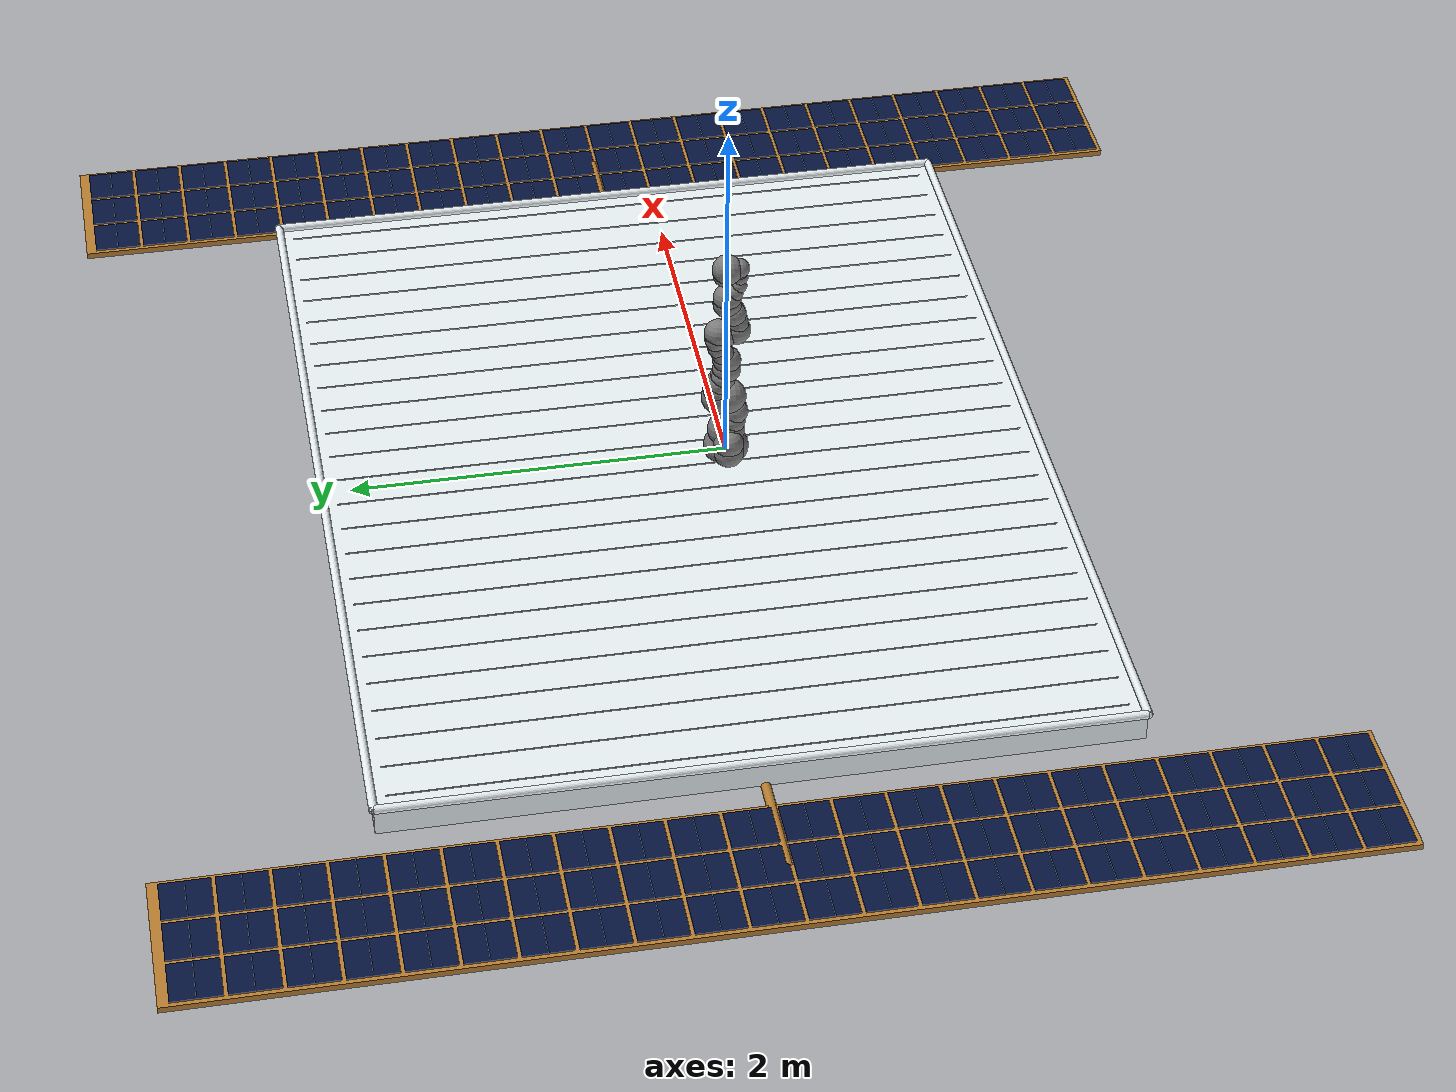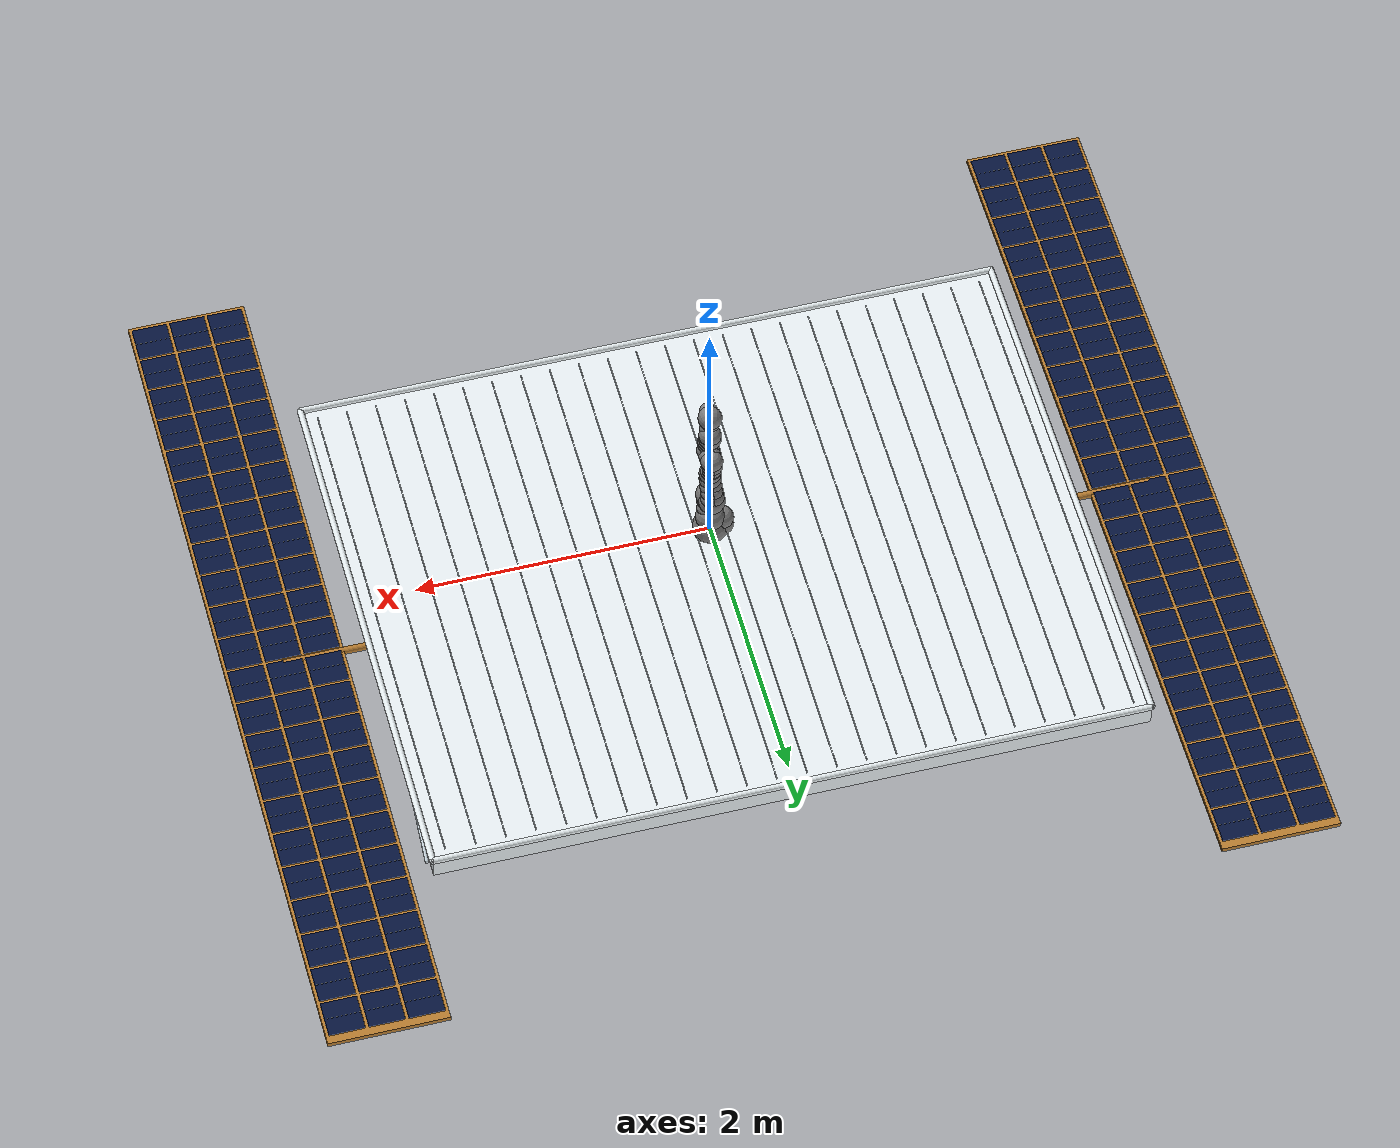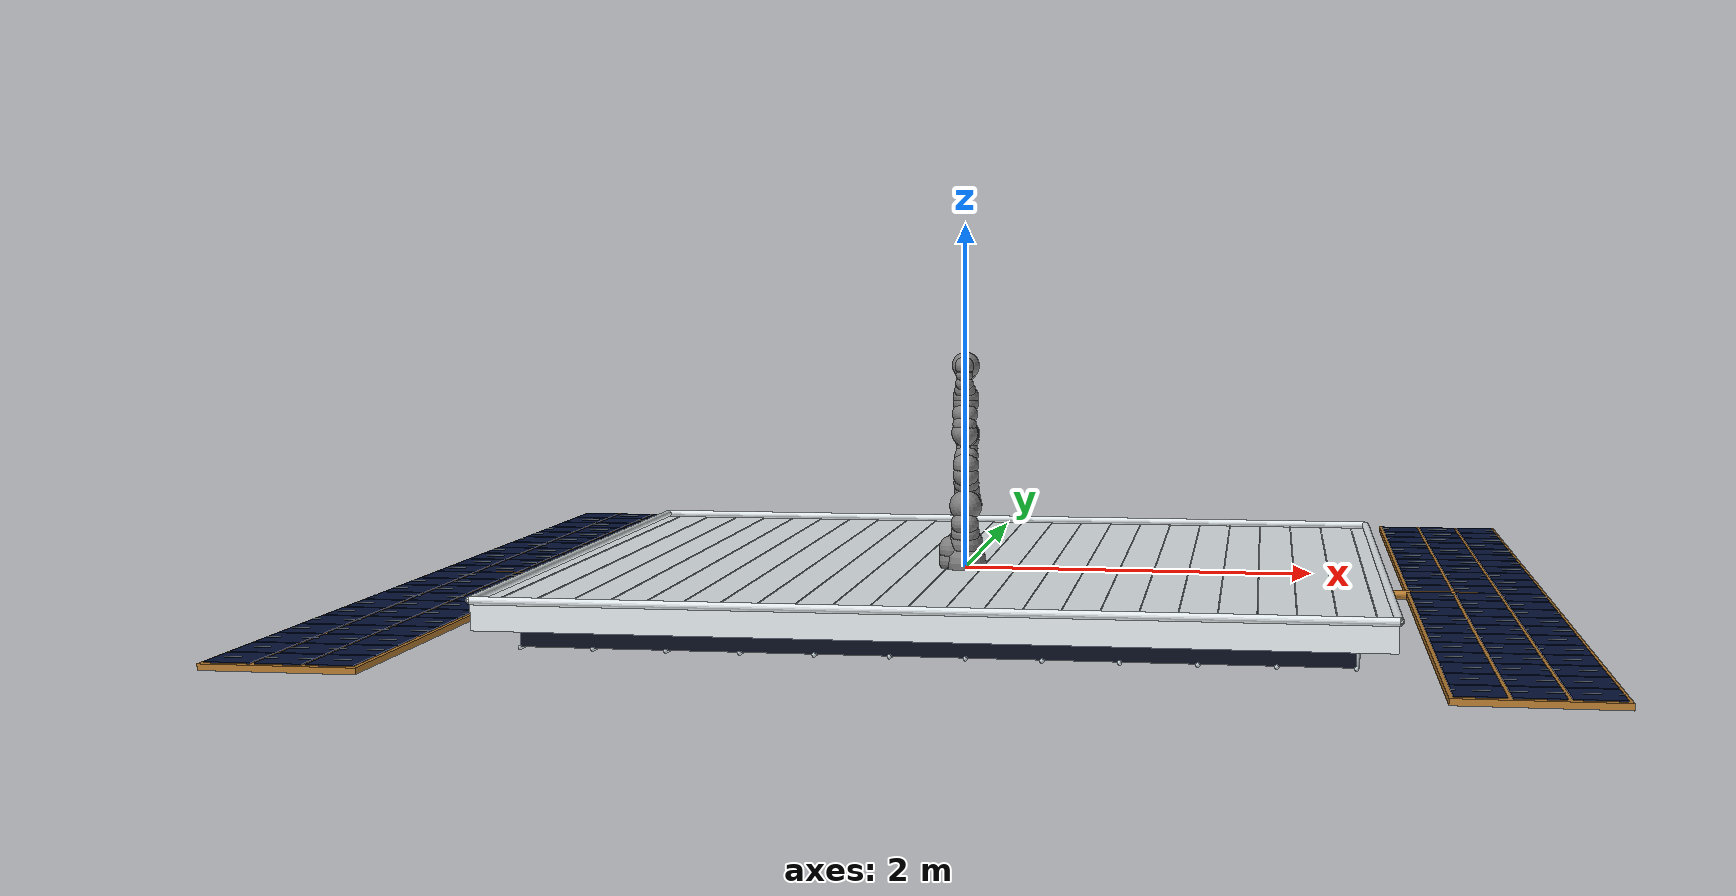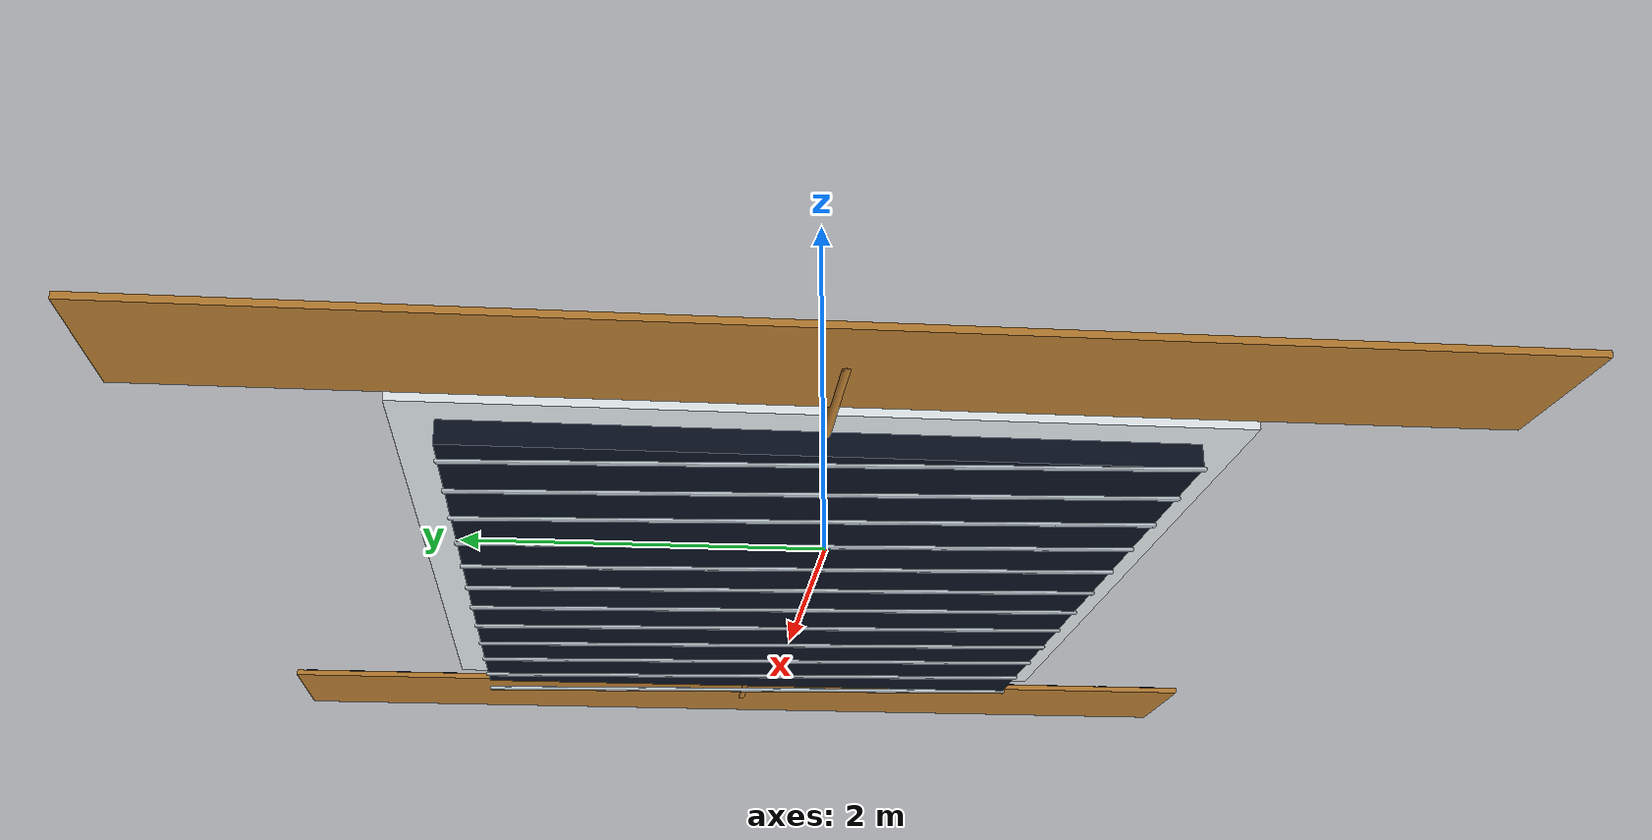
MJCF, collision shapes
<mujoco model="iiwa14">
  <compiler angle="degree" meshdir="/home/xiao/workspace/maintained/compliant_docking_simulation/assets/iiwa14/assets" />
  <option integrator="implicitfast" gravity="0 0 0" timestep="0.001" cone="elliptic" sdf_iterations="10" sdf_initpoints="40" />
  <size nconmax="500000" njmax="5000" />
  <visual>
    <scale forcewidth="0.01" framewidth="0.01" contactwidth="0.01" />
    <map force="0.1" />
    <global offwidth="1920" offheight="1080" />
    <headlight ambient=".28 .30 .36" diffuse=".65 .68 .75" specular=".18 .18 .18" />
  </visual>
  <default>
    <default class="iiwa">
      <material specular="0.5" shininess="0.25" />
      <default class="visual">
        <geom type="mesh" contype="0" conaffinity="0" group="2" material="gray" />
      </default>
      <default class="collision">
        <geom group="3" />
      </default>
      <site size="0.001" rgba="1 0 0 1" group="4" />
    </default>
    <joint armature="0" damping="0" limited="false" />
  </default>
  <asset>
    <texture name="grid" type="2d" builtin="checker" width="512" height="512" rgb1=".1 .2 .3" rgb2=".2 .3 .4" />
    <material name="grid" texture="grid" texrepeat="1 1" texuniform="true" reflectance="0." />
    <texture type="skybox" builtin="gradient" rgb1=".34 .47 .60" rgb2=".12 .22 .34" width="1024" height="6144" mark="random" markrgb=".90 .94 1" random=".0015" />
    <texture type="2d" name="groundplane" builtin="checker" mark="edge" rgb1="0.2 0.3 0.4" rgb2="0.1 0.2 0.3" markrgb="0.8 0.8 0.8" width="300" height="300" />
    <material name="groundplane" texture="groundplane" texuniform="true" texrepeat="5 5" reflectance="0.2" rgba="0 0 0 0" />
    <material class="iiwa" name="gray" rgba=".87 .91 .94 1" />
    <material class="iiwa" name="light_gray" rgba=".87 .91 .94 1" />
    <material class="iiwa" name="black" rgba="0 0 0 1" />
    <material class="iiwa" name="orange" rgba=".22 .35 .48 1" />
    <mesh file="link_0.obj" />
    <mesh file="link_1.obj" />
    <mesh file="link_2_orange.obj" />
    <mesh file="link_2_grey.obj" />
    <mesh file="link_3.obj" />
    <mesh file="band.obj" />
    <mesh file="kuka.obj" />
    <mesh file="link_4_orange.obj" />
    <mesh file="link_4_grey.obj" />
    <mesh file="link_5.obj" />
    <mesh file="link_6_orange.obj" />
    <mesh file="link_6_grey.obj" />
    <mesh file="link_7.obj" />
    <material name="part_material" rgba="0.7 0.7 0.7 1" />
    <material name="orb_metal" rgba="0.78 0.83 0.86 1" specular="0.65" shininess="0.5" />
    <material name="orb_white" rgba="0.91 0.9399999999999999 0.95 1" specular="0.35" shininess="0.5" />
    <material name="orb_blue" rgba="0.12 0.32 0.88 1" specular="0.55" shininess="0.5" />
    <material name="orb_dark" rgba="0.035 0.06 0.12 1" specular="0.22" shininess="0.5" />
    <material name="orb_gold" rgba="0.72 0.49 0.19 1" specular="0.55" shininess="0.5" />
    <material name="orb_cyan" rgba="0.12 0.78 0.9 1" specular="0.4" shininess="0.5" />
    <material name="orb_cell" rgba="0.025 0.08 0.24 1" specular="0.7" shininess="0.5" />
  </asset>
  <worldbody>
    <body name="base" childclass="iiwa">
      <inertial mass="5" pos="-0.1 0 0.07" diaginertia="0.05 0.06 0.03" />
      <geom class="visual" mesh="link_0" />
      <geom class="collision" size="0.12" pos="0 0 0.03" />
      <geom class="collision" size="0.08" pos="-0.08 0 0.103" />
      <geom class="collision" size="0.08" pos="-0.08 0 0.04" />
      <geom class="collision" size="0.1" pos="0 0 0.14" />
      <body name="link1" pos="0 0 0.1575">
        <inertial mass="4" pos="0 -0.03 0.12" diaginertia="0.1 0.09 0.02" />
        <joint name="joint1" pos="0 0 0" axis="0 0 1" />
        <geom class="visual" mesh="link_1" />
        <geom class="collision" size="0.08" pos="0 0 -0.0005" />
        <geom class="collision" size="0.075" pos="0.01 -0.025 0.0425" />
        <geom class="collision" size="0.075" pos="-0.01 -0.025 0.0425" />
        <geom class="collision" size="0.07" pos="0.01 -0.045 0.1025" />
        <geom class="collision" size="0.07" pos="-0.01 -0.045 0.1025" />
        <body name="link2" pos="0 0 0.2025" quat="0 0 1 1">
          <inertial mass="4" pos="0.0003 0.059 0.042" diaginertia="0.05 0.044 0.018" quat="0.707107 0.707107 0 0" />
          <joint name="joint2" pos="0 0 0" axis="0 0 1" />
          <geom class="visual" material="orange" mesh="link_2_orange" />
          <geom class="visual" mesh="link_2_grey" />
          <geom class="collision" size="0.095" pos="0 0 -0.01" />
          <geom class="collision" size="0.09" pos="0 0 0.045" />
          <geom class="collision" size="0.07" pos="-0.01 0.04 0.054" />
          <geom class="collision" size="0.065" pos="-0.01 0.09 0.04" />
          <geom class="collision" size="0.065" pos="-0.01 0.13 0.02" />
          <geom class="collision" size="0.07" pos="0.01 0.04 0.054" />
          <geom class="collision" size="0.065" pos="0.01 0.09 0.04" />
          <geom class="collision" size="0.065" pos="0.01 0.13 0.02" />
          <geom class="collision" size="0.075" pos="0 0.18 0" />
          <body name="link3" pos="0 0.2045 0" quat="0 0 1 1">
            <inertial mass="3" pos="0 0.03 0.13" diaginertia="0.025 0.0238 0.0076" />
            <joint name="joint3" pos="0 0 0" axis="0 0 1" />
            <geom class="visual" mesh="link_3" />
            <geom class="visual" material="light_gray" mesh="band" />
            <geom class="visual" material="black" mesh="kuka" />
            <geom class="collision" size="0.075" pos="0 0 0.0355" />
            <geom class="collision" size="0.06" pos="0.01 0.023 0.0855" />
            <geom class="collision" size="0.055" pos="0.01 0.048 0.1255" />
            <geom class="collision" size="0.06" pos="0.01 0.056 0.1755" />
            <geom class="collision" size="0.06" pos="-0.01 0.023 0.0855" />
            <geom class="collision" size="0.055" pos="-0.01 0.048 0.1255" />
            <geom class="collision" size="0.06" pos="-0.01 0.056 0.1755" />
            <geom class="collision" size="0.075" pos="0 0.045 0.2155" />
            <geom class="collision" size="0.075" pos="0 0 0.2155" />
            <body name="link4" pos="0 0 0.2155" quat="1 1 0 0">
              <inertial mass="2.7" pos="0 0.067 0.034" diaginertia="0.03 0.029 0.01" quat="1 1 0 0" />
              <joint name="joint4" pos="0 0 0" axis="0 0 1" />
              <geom class="visual" material="orange" mesh="link_4_orange" />
              <geom class="visual" mesh="link_4_grey" />
              <geom class="collision" size="0.078" pos="0 0.01 0.046" />
              <geom class="collision" size="0.06" pos="0.01 0.06 0.052" />
              <geom class="collision" size="0.065" pos="0.01 0.12 0.034" />
              <geom class="collision" size="0.06" pos="-0.01 0.06 0.052" />
              <geom class="collision" size="0.065" pos="-0.01 0.12 0.034" />
              <geom class="collision" size="0.075" pos="0 0.184 0" />
              <body name="link5" pos="0 0.1845 0" quat="0 0 1 1">
                <inertial mass="1.7" pos="0.0001 0.021 0.076" diaginertia="0.02 0.018 0.005" />
                <joint name="joint5" pos="0 0 0" axis="0 0 1" />
                <geom class="visual" mesh="link_5" />
                <geom class="visual" material="light_gray" mesh="band" />
                <geom class="visual" material="black" mesh="kuka" />
                <geom class="collision" size="0.075" pos="0 0 0.0335" />
                <geom class="collision" size="0.05" pos="-0.012 0.031 0.0755" />
                <geom class="collision" size="0.05" pos="0.012 0.031 0.0755" />
                <geom class="collision" size="0.04" pos="-0.012 0.06 0.1155" />
                <geom class="collision" size="0.04" pos="0.012 0.06 0.1155" />
                <geom class="collision" size="0.04" pos="-0.01 0.065 0.1655" />
                <geom class="collision" size="0.04" pos="0.01 0.065 0.1655" />
                <geom class="collision" size="0.035" pos="-0.012 0.065 0.1855" />
                <geom class="collision" size="0.035" pos="0.012 0.065 0.1855" />
                <body name="link6" pos="0 0 0.2155" quat="1 1 0 0">
                  <inertial mass="1.8" pos="0 0.0006 0.0004" diaginertia="0.005 0.0047 0.0036" quat="1 1 0 0" />
                  <joint name="joint6" pos="0 0 0" axis="0 0 1" />
                  <geom class="visual" material="orange" mesh="link_6_orange" />
                  <geom class="visual" mesh="link_6_grey" />
                  <geom class="collision" size="0.055" pos="0 0 -0.059" />
                  <geom class="collision" size="0.065" pos="0 -0.03 0.011" />
                  <geom class="collision" size="0.08" />
                  <body name="link7" pos="0 0.081 0" quat="0 0 1 1">
                    <inertial mass="0.3" pos="0 0 0.02" diaginertia="0.001 0.001 0.001" />
                    <joint name="joint7" pos="0 0 0" axis="0 0 1" />
                    <geom class="visual" mesh="link_7" />
                    <site pos="0 0 0.045" name="attachment_site" />
                  </body>
                </body>
              </body>
            </body>
          </body>
        </body>
      </body>
    </body>
    <body name="orbital_platform">
      <geom type="box" material="orb_white" contype="0" conaffinity="0" mass="0" group="4" pos="0 0.25 -0.075" size="2.4 1.9 0.07000000000000001" />
      <geom type="box" material="orb_dark" contype="0" conaffinity="0" mass="0" group="4" pos="0 0.25 -0.2" size="2.2 1.7 0.06" />
      <geom type="capsule" material="orb_metal" contype="0" conaffinity="0" mass="0" group="4" fromto="-2.3 -1.58 0.001 -2.3 2.08 0.001" size="0.003" />
      <geom type="capsule" material="orb_metal" contype="0" conaffinity="0" mass="0" group="4" fromto="-2.1 -1.58 0.001 -2.1 2.08 0.001" size="0.003" />
      <geom type="capsule" material="orb_metal" contype="0" conaffinity="0" mass="0" group="4" fromto="-1.9 -1.58 0.001 -1.9 2.08 0.001" size="0.003" />
      <geom type="capsule" material="orb_metal" contype="0" conaffinity="0" mass="0" group="4" fromto="-1.7 -1.58 0.001 -1.7 2.08 0.001" size="0.003" />
      <geom type="capsule" material="orb_metal" contype="0" conaffinity="0" mass="0" group="4" fromto="-1.5 -1.58 0.001 -1.5 2.08 0.001" size="0.003" />
      <geom type="capsule" material="orb_metal" contype="0" conaffinity="0" mass="0" group="4" fromto="-1.3 -1.58 0.001 -1.3 2.08 0.001" size="0.003" />
      <geom type="capsule" material="orb_metal" contype="0" conaffinity="0" mass="0" group="4" fromto="-1.1 -1.58 0.001 -1.1 2.08 0.001" size="0.003" />
      <geom type="capsule" material="orb_metal" contype="0" conaffinity="0" mass="0" group="4" fromto="-0.8999999999999999 -1.58 0.001 -0.8999999999999999 2.08 0.001" size="0.003" />
      <geom type="capsule" material="orb_metal" contype="0" conaffinity="0" mass="0" group="4" fromto="-0.7 -1.58 0.001 -0.7 2.08 0.001" size="0.003" />
      <geom type="capsule" material="orb_metal" contype="0" conaffinity="0" mass="0" group="4" fromto="-0.5 -1.58 0.001 -0.5 2.08 0.001" size="0.003" />
      <geom type="capsule" material="orb_metal" contype="0" conaffinity="0" mass="0" group="4" fromto="-0.3 -1.58 0.001 -0.3 2.08 0.001" size="0.003" />
      <geom type="capsule" material="orb_metal" contype="0" conaffinity="0" mass="0" group="4" fromto="-0.1000000000000001 -1.58 0.001 -0.1000000000000001 2.08 0.001" size="0.003" />
      <geom type="capsule" material="orb_metal" contype="0" conaffinity="0" mass="0" group="4" fromto="0.1000000000000001 -1.58 0.001 0.1000000000000001 2.08 0.001" size="0.003" />
      <geom type="capsule" material="orb_metal" contype="0" conaffinity="0" mass="0" group="4" fromto="0.2999999999999998 -1.58 0.001 0.2999999999999998 2.08 0.001" size="0.003" />
      <geom type="capsule" material="orb_metal" contype="0" conaffinity="0" mass="0" group="4" fromto="0.5 -1.58 0.001 0.5 2.08 0.001" size="0.003" />
      <geom type="capsule" material="orb_metal" contype="0" conaffinity="0" mass="0" group="4" fromto="0.6999999999999997 -1.58 0.001 0.6999999999999997 2.08 0.001" size="0.003" />
      <geom type="capsule" material="orb_metal" contype="0" conaffinity="0" mass="0" group="4" fromto="0.8999999999999999 -1.58 0.001 0.8999999999999999 2.08 0.001" size="0.003" />
      <geom type="capsule" material="orb_metal" contype="0" conaffinity="0" mass="0" group="4" fromto="1.1 -1.58 0.001 1.1 2.08 0.001" size="0.003" />
      <geom type="capsule" material="orb_metal" contype="0" conaffinity="0" mass="0" group="4" fromto="1.3 -1.58 0.001 1.3 2.08 0.001" size="0.003" />
      <geom type="capsule" material="orb_metal" contype="0" conaffinity="0" mass="0" group="4" fromto="1.5 -1.58 0.001 1.5 2.08 0.001" size="0.003" />
      <geom type="capsule" material="orb_metal" contype="0" conaffinity="0" mass="0" group="4" fromto="1.7 -1.58 0.001 1.7 2.08 0.001" size="0.003" />
      <geom type="capsule" material="orb_metal" contype="0" conaffinity="0" mass="0" group="4" fromto="1.899999999999999 -1.58 0.001 1.899999999999999 2.08 0.001" size="0.003" />
      <geom type="capsule" material="orb_metal" contype="0" conaffinity="0" mass="0" group="4" fromto="2.1 -1.58 0.001 2.1 2.08 0.001" size="0.003" />
      <geom type="capsule" material="orb_metal" contype="0" conaffinity="0" mass="0" group="4" fromto="2.3 -1.58 0.001 2.3 2.08 0.001" size="0.003" />
      <geom type="capsule" material="orb_white" contype="0" conaffinity="0" mass="0" group="4" fromto="-2.4 -1.65 0.015 -2.4 2.15 0.015" size="0.022" />
      <geom type="capsule" material="orb_white" contype="0" conaffinity="0" mass="0" group="4" fromto="2.4 -1.65 0.015 2.4 2.15 0.015" size="0.022" />
      <geom type="capsule" material="orb_white" contype="0" conaffinity="0" mass="0" group="4" fromto="-2.4 -1.65 0.015 2.4 -1.65 0.015" size="0.022" />
      <geom type="capsule" material="orb_white" contype="0" conaffinity="0" mass="0" group="4" fromto="-2.4 2.15 0.015 2.4 2.15 0.015" size="0.022" />
      <geom type="capsule" material="orb_metal" contype="0" conaffinity="0" mass="0" group="4" fromto="-2.2 -1.45 -0.265 -2 1.95 -0.265" size="0.012" />
      <geom type="capsule" material="orb_metal" contype="0" conaffinity="0" mass="0" group="4" fromto="-1.8 -1.45 -0.265 -1.6 1.95 -0.265" size="0.012" />
      <geom type="capsule" material="orb_metal" contype="0" conaffinity="0" mass="0" group="4" fromto="-1.4 -1.45 -0.265 -1.2 1.95 -0.265" size="0.012" />
      <geom type="capsule" material="orb_metal" contype="0" conaffinity="0" mass="0" group="4" fromto="-1 -1.45 -0.265 -0.8 1.95 -0.265" size="0.012" />
      <geom type="capsule" material="orb_metal" contype="0" conaffinity="0" mass="0" group="4" fromto="-0.6000000000000001 -1.45 -0.265 -0.4000000000000001 1.95 -0.265" size="0.012" />
      <geom type="capsule" material="orb_metal" contype="0" conaffinity="0" mass="0" group="4" fromto="-0.2000000000000002 -1.45 -0.265 -1.665334536937735e-16 1.95 -0.265" size="0.012" />
      <geom type="capsule" material="orb_metal" contype="0" conaffinity="0" mass="0" group="4" fromto="0.2000000000000002 -1.45 -0.265 0.4000000000000002 1.95 -0.265" size="0.012" />
      <geom type="capsule" material="orb_metal" contype="0" conaffinity="0" mass="0" group="4" fromto="0.6000000000000001 -1.45 -0.265 0.8 1.95 -0.265" size="0.012" />
      <geom type="capsule" material="orb_metal" contype="0" conaffinity="0" mass="0" group="4" fromto="1 -1.45 -0.265 1.2 1.95 -0.265" size="0.012" />
      <geom type="capsule" material="orb_metal" contype="0" conaffinity="0" mass="0" group="4" fromto="1.4 -1.45 -0.265 1.6 1.95 -0.265" size="0.012" />
      <geom type="capsule" material="orb_metal" contype="0" conaffinity="0" mass="0" group="4" fromto="1.8 -1.45 -0.265 2 1.95 -0.265" size="0.012" />
      <geom type="capsule" material="orb_metal" contype="0" conaffinity="0" mass="0" group="4" fromto="2.2 -1.45 -0.265 2.4 1.95 -0.265" size="0.012" />
      <geom type="capsule" material="orb_gold" contype="0" conaffinity="0" mass="0" group="4" fromto="-2.2 0.25 -0.15 -2.95 0.25 -0.15" size="0.025" />
      <geom type="box" material="orb_gold" contype="0" conaffinity="0" mass="0" group="4" pos="-2.95 0.25 -0.15" size="0.4 3 0.016" />
      <geom type="box" material="orb_cell" contype="0" conaffinity="0" mass="0" group="4" pos="-2.69 -2.6 -0.13" size="0.119 0.125 0.003" />
      <geom type="capsule" material="orb_metal" contype="0" conaffinity="0" mass="0" group="4" fromto="-2.81 -2.6 -0.126 -2.57 -2.6 -0.126" size="0.0012" />
      <geom type="box" material="orb_cell" contype="0" conaffinity="0" mass="0" group="4" pos="-2.69 -2.33 -0.13" size="0.119 0.125 0.003" />
      <geom type="capsule" material="orb_metal" contype="0" conaffinity="0" mass="0" group="4" fromto="-2.81 -2.33 -0.126 -2.57 -2.33 -0.126" size="0.0012" />
      <geom type="box" material="orb_cell" contype="0" conaffinity="0" mass="0" group="4" pos="-2.69 -2.06 -0.13" size="0.119 0.125 0.003" />
      <geom type="capsule" material="orb_metal" contype="0" conaffinity="0" mass="0" group="4" fromto="-2.81 -2.06 -0.126 -2.57 -2.06 -0.126" size="0.0012" />
      <geom type="box" material="orb_cell" contype="0" conaffinity="0" mass="0" group="4" pos="-2.69 -1.79 -0.13" size="0.119 0.125 0.003" />
      <geom type="capsule" material="orb_metal" contype="0" conaffinity="0" mass="0" group="4" fromto="-2.81 -1.79 -0.126 -2.57 -1.79 -0.126" size="0.0012" />
      <geom type="box" material="orb_cell" contype="0" conaffinity="0" mass="0" group="4" pos="-2.69 -1.52 -0.13" size="0.119 0.125 0.003" />
      <geom type="capsule" material="orb_metal" contype="0" conaffinity="0" mass="0" group="4" fromto="-2.81 -1.52 -0.126 -2.57 -1.52 -0.126" size="0.0012" />
      <geom type="box" material="orb_cell" contype="0" conaffinity="0" mass="0" group="4" pos="-2.69 -1.25 -0.13" size="0.119 0.125 0.003" />
      <geom type="capsule" material="orb_metal" contype="0" conaffinity="0" mass="0" group="4" fromto="-2.81 -1.25 -0.126 -2.57 -1.25 -0.126" size="0.0012" />
      <geom type="box" material="orb_cell" contype="0" conaffinity="0" mass="0" group="4" pos="-2.69 -0.98 -0.13" size="0.119 0.125 0.003" />
      <geom type="capsule" material="orb_metal" contype="0" conaffinity="0" mass="0" group="4" fromto="-2.81 -0.98 -0.126 -2.57 -0.98 -0.126" size="0.0012" />
      <geom type="box" material="orb_cell" contype="0" conaffinity="0" mass="0" group="4" pos="-2.69 -0.71 -0.13" size="0.119 0.125 0.003" />
      <geom type="capsule" material="orb_metal" contype="0" conaffinity="0" mass="0" group="4" fromto="-2.81 -0.71 -0.126 -2.57 -0.71 -0.126" size="0.0012" />
      <geom type="box" material="orb_cell" contype="0" conaffinity="0" mass="0" group="4" pos="-2.69 -0.4399999999999999 -0.13" size="0.119 0.125 0.003" />
      <geom type="capsule" material="orb_metal" contype="0" conaffinity="0" mass="0" group="4" fromto="-2.81 -0.4399999999999999 -0.126 -2.57 -0.4399999999999999 -0.126" size="0.0012" />
      <geom type="box" material="orb_cell" contype="0" conaffinity="0" mass="0" group="4" pos="-2.69 -0.1699999999999999 -0.13" size="0.119 0.125 0.003" />
      <geom type="capsule" material="orb_metal" contype="0" conaffinity="0" mass="0" group="4" fromto="-2.81 -0.1699999999999999 -0.126 -2.57 -0.1699999999999999 -0.126" size="0.0012" />
      <geom type="box" material="orb_cell" contype="0" conaffinity="0" mass="0" group="4" pos="-2.69 0.1000000000000001 -0.13" size="0.119 0.125 0.003" />
      <geom type="capsule" material="orb_metal" contype="0" conaffinity="0" mass="0" group="4" fromto="-2.81 0.1000000000000001 -0.126 -2.57 0.1000000000000001 -0.126" size="0.0012" />
      <geom type="box" material="orb_cell" contype="0" conaffinity="0" mass="0" group="4" pos="-2.69 0.3700000000000001 -0.13" size="0.119 0.125 0.003" />
      <geom type="capsule" material="orb_metal" contype="0" conaffinity="0" mass="0" group="4" fromto="-2.81 0.3700000000000001 -0.126 -2.57 0.3700000000000001 -0.126" size="0.0012" />
      <geom type="box" material="orb_cell" contype="0" conaffinity="0" mass="0" group="4" pos="-2.69 0.6400000000000001 -0.13" size="0.119 0.125 0.003" />
      <geom type="capsule" material="orb_metal" contype="0" conaffinity="0" mass="0" group="4" fromto="-2.81 0.6400000000000001 -0.126 -2.57 0.6400000000000001 -0.126" size="0.0012" />
      <geom type="box" material="orb_cell" contype="0" conaffinity="0" mass="0" group="4" pos="-2.69 0.9100000000000001 -0.13" size="0.119 0.125 0.003" />
      <geom type="capsule" material="orb_metal" contype="0" conaffinity="0" mass="0" group="4" fromto="-2.81 0.9100000000000001 -0.126 -2.57 0.9100000000000001 -0.126" size="0.0012" />
      <geom type="box" material="orb_cell" contype="0" conaffinity="0" mass="0" group="4" pos="-2.69 1.18 -0.13" size="0.119 0.125 0.003" />
      <geom type="capsule" material="orb_metal" contype="0" conaffinity="0" mass="0" group="4" fromto="-2.81 1.18 -0.126 -2.57 1.18 -0.126" size="0.0012" />
      <geom type="box" material="orb_cell" contype="0" conaffinity="0" mass="0" group="4" pos="-2.69 1.450000000000001 -0.13" size="0.119 0.125 0.003" />
      <geom type="capsule" material="orb_metal" contype="0" conaffinity="0" mass="0" group="4" fromto="-2.81 1.450000000000001 -0.126 -2.57 1.450000000000001 -0.126" size="0.0012" />
      <geom type="box" material="orb_cell" contype="0" conaffinity="0" mass="0" group="4" pos="-2.69 1.72 -0.13" size="0.119 0.125 0.003" />
      <geom type="capsule" material="orb_metal" contype="0" conaffinity="0" mass="0" group="4" fromto="-2.81 1.72 -0.126 -2.57 1.72 -0.126" size="0.0012" />
      <geom type="box" material="orb_cell" contype="0" conaffinity="0" mass="0" group="4" pos="-2.69 1.99 -0.13" size="0.119 0.125 0.003" />
      <geom type="capsule" material="orb_metal" contype="0" conaffinity="0" mass="0" group="4" fromto="-2.81 1.99 -0.126 -2.57 1.99 -0.126" size="0.0012" />
      <geom type="box" material="orb_cell" contype="0" conaffinity="0" mass="0" group="4" pos="-2.69 2.26 -0.13" size="0.119 0.125 0.003" />
      <geom type="capsule" material="orb_metal" contype="0" conaffinity="0" mass="0" group="4" fromto="-2.81 2.26 -0.126 -2.57 2.26 -0.126" size="0.0012" />
      <geom type="box" material="orb_cell" contype="0" conaffinity="0" mass="0" group="4" pos="-2.69 2.530000000000001 -0.13" size="0.119 0.125 0.003" />
      <geom type="capsule" material="orb_metal" contype="0" conaffinity="0" mass="0" group="4" fromto="-2.81 2.530000000000001 -0.126 -2.57 2.530000000000001 -0.126" size="0.0012" />
      <geom type="box" material="orb_cell" contype="0" conaffinity="0" mass="0" group="4" pos="-2.69 2.8 -0.13" size="0.119 0.125 0.003" />
      <geom type="capsule" material="orb_metal" contype="0" conaffinity="0" mass="0" group="4" fromto="-2.81 2.8 -0.126 -2.57 2.8 -0.126" size="0.0012" />
      <geom type="box" material="orb_cell" contype="0" conaffinity="0" mass="0" group="4" pos="-2.69 3.07 -0.13" size="0.119 0.125 0.003" />
      <geom type="capsule" material="orb_metal" contype="0" conaffinity="0" mass="0" group="4" fromto="-2.81 3.07 -0.126 -2.57 3.07 -0.126" size="0.0012" />
      <geom type="box" material="orb_cell" contype="0" conaffinity="0" mass="0" group="4" pos="-2.95 -2.6 -0.13" size="0.119 0.125 0.003" />
      <geom type="capsule" material="orb_metal" contype="0" conaffinity="0" mass="0" group="4" fromto="-3.07 -2.6 -0.126 -2.83 -2.6 -0.126" size="0.0012" />
      <geom type="box" material="orb_cell" contype="0" conaffinity="0" mass="0" group="4" pos="-2.95 -2.33 -0.13" size="0.119 0.125 0.003" />
      <geom type="capsule" material="orb_metal" contype="0" conaffinity="0" mass="0" group="4" fromto="-3.07 -2.33 -0.126 -2.83 -2.33 -0.126" size="0.0012" />
      <geom type="box" material="orb_cell" contype="0" conaffinity="0" mass="0" group="4" pos="-2.95 -2.06 -0.13" size="0.119 0.125 0.003" />
      <geom type="capsule" material="orb_metal" contype="0" conaffinity="0" mass="0" group="4" fromto="-3.07 -2.06 -0.126 -2.83 -2.06 -0.126" size="0.0012" />
      <geom type="box" material="orb_cell" contype="0" conaffinity="0" mass="0" group="4" pos="-2.95 -1.79 -0.13" size="0.119 0.125 0.003" />
      <geom type="capsule" material="orb_metal" contype="0" conaffinity="0" mass="0" group="4" fromto="-3.07 -1.79 -0.126 -2.83 -1.79 -0.126" size="0.0012" />
      <geom type="box" material="orb_cell" contype="0" conaffinity="0" mass="0" group="4" pos="-2.95 -1.52 -0.13" size="0.119 0.125 0.003" />
      <geom type="capsule" material="orb_metal" contype="0" conaffinity="0" mass="0" group="4" fromto="-3.07 -1.52 -0.126 -2.83 -1.52 -0.126" size="0.0012" />
      <geom type="box" material="orb_cell" contype="0" conaffinity="0" mass="0" group="4" pos="-2.95 -1.25 -0.13" size="0.119 0.125 0.003" />
      <geom type="capsule" material="orb_metal" contype="0" conaffinity="0" mass="0" group="4" fromto="-3.07 -1.25 -0.126 -2.83 -1.25 -0.126" size="0.0012" />
      <geom type="box" material="orb_cell" contype="0" conaffinity="0" mass="0" group="4" pos="-2.95 -0.98 -0.13" size="0.119 0.125 0.003" />
      <geom type="capsule" material="orb_metal" contype="0" conaffinity="0" mass="0" group="4" fromto="-3.07 -0.98 -0.126 -2.83 -0.98 -0.126" size="0.0012" />
      <geom type="box" material="orb_cell" contype="0" conaffinity="0" mass="0" group="4" pos="-2.95 -0.71 -0.13" size="0.119 0.125 0.003" />
      <geom type="capsule" material="orb_metal" contype="0" conaffinity="0" mass="0" group="4" fromto="-3.07 -0.71 -0.126 -2.83 -0.71 -0.126" size="0.0012" />
      <geom type="box" material="orb_cell" contype="0" conaffinity="0" mass="0" group="4" pos="-2.95 -0.4399999999999999 -0.13" size="0.119 0.125 0.003" />
      <geom type="capsule" material="orb_metal" contype="0" conaffinity="0" mass="0" group="4" fromto="-3.07 -0.4399999999999999 -0.126 -2.83 -0.4399999999999999 -0.126" size="0.0012" />
      <geom type="box" material="orb_cell" contype="0" conaffinity="0" mass="0" group="4" pos="-2.95 -0.1699999999999999 -0.13" size="0.119 0.125 0.003" />
      <geom type="capsule" material="orb_metal" contype="0" conaffinity="0" mass="0" group="4" fromto="-3.07 -0.1699999999999999 -0.126 -2.83 -0.1699999999999999 -0.126" size="0.0012" />
      <geom type="box" material="orb_cell" contype="0" conaffinity="0" mass="0" group="4" pos="-2.95 0.1000000000000001 -0.13" size="0.119 0.125 0.003" />
      <geom type="capsule" material="orb_metal" contype="0" conaffinity="0" mass="0" group="4" fromto="-3.07 0.1000000000000001 -0.126 -2.83 0.1000000000000001 -0.126" size="0.0012" />
      <geom type="box" material="orb_cell" contype="0" conaffinity="0" mass="0" group="4" pos="-2.95 0.3700000000000001 -0.13" size="0.119 0.125 0.003" />
      <geom type="capsule" material="orb_metal" contype="0" conaffinity="0" mass="0" group="4" fromto="-3.07 0.3700000000000001 -0.126 -2.83 0.3700000000000001 -0.126" size="0.0012" />
      <geom type="box" material="orb_cell" contype="0" conaffinity="0" mass="0" group="4" pos="-2.95 0.6400000000000001 -0.13" size="0.119 0.125 0.003" />
      <geom type="capsule" material="orb_metal" contype="0" conaffinity="0" mass="0" group="4" fromto="-3.07 0.6400000000000001 -0.126 -2.83 0.6400000000000001 -0.126" size="0.0012" />
      <geom type="box" material="orb_cell" contype="0" conaffinity="0" mass="0" group="4" pos="-2.95 0.9100000000000001 -0.13" size="0.119 0.125 0.003" />
      <geom type="capsule" material="orb_metal" contype="0" conaffinity="0" mass="0" group="4" fromto="-3.07 0.9100000000000001 -0.126 -2.83 0.9100000000000001 -0.126" size="0.0012" />
      <geom type="box" material="orb_cell" contype="0" conaffinity="0" mass="0" group="4" pos="-2.95 1.18 -0.13" size="0.119 0.125 0.003" />
      <geom type="capsule" material="orb_metal" contype="0" conaffinity="0" mass="0" group="4" fromto="-3.07 1.18 -0.126 -2.83 1.18 -0.126" size="0.0012" />
      <geom type="box" material="orb_cell" contype="0" conaffinity="0" mass="0" group="4" pos="-2.95 1.450000000000001 -0.13" size="0.119 0.125 0.003" />
      <geom type="capsule" material="orb_metal" contype="0" conaffinity="0" mass="0" group="4" fromto="-3.07 1.450000000000001 -0.126 -2.83 1.450000000000001 -0.126" size="0.0012" />
      <geom type="box" material="orb_cell" contype="0" conaffinity="0" mass="0" group="4" pos="-2.95 1.72 -0.13" size="0.119 0.125 0.003" />
      <geom type="capsule" material="orb_metal" contype="0" conaffinity="0" mass="0" group="4" fromto="-3.07 1.72 -0.126 -2.83 1.72 -0.126" size="0.0012" />
      <geom type="box" material="orb_cell" contype="0" conaffinity="0" mass="0" group="4" pos="-2.95 1.99 -0.13" size="0.119 0.125 0.003" />
      <geom type="capsule" material="orb_metal" contype="0" conaffinity="0" mass="0" group="4" fromto="-3.07 1.99 -0.126 -2.83 1.99 -0.126" size="0.0012" />
      <geom type="box" material="orb_cell" contype="0" conaffinity="0" mass="0" group="4" pos="-2.95 2.26 -0.13" size="0.119 0.125 0.003" />
      <geom type="capsule" material="orb_metal" contype="0" conaffinity="0" mass="0" group="4" fromto="-3.07 2.26 -0.126 -2.83 2.26 -0.126" size="0.0012" />
      <geom type="box" material="orb_cell" contype="0" conaffinity="0" mass="0" group="4" pos="-2.95 2.530000000000001 -0.13" size="0.119 0.125 0.003" />
      <geom type="capsule" material="orb_metal" contype="0" conaffinity="0" mass="0" group="4" fromto="-3.07 2.530000000000001 -0.126 -2.83 2.530000000000001 -0.126" size="0.0012" />
      <geom type="box" material="orb_cell" contype="0" conaffinity="0" mass="0" group="4" pos="-2.95 2.8 -0.13" size="0.119 0.125 0.003" />
      <geom type="capsule" material="orb_metal" contype="0" conaffinity="0" mass="0" group="4" fromto="-3.07 2.8 -0.126 -2.83 2.8 -0.126" size="0.0012" />
      <geom type="box" material="orb_cell" contype="0" conaffinity="0" mass="0" group="4" pos="-2.95 3.07 -0.13" size="0.119 0.125 0.003" />
      <geom type="capsule" material="orb_metal" contype="0" conaffinity="0" mass="0" group="4" fromto="-3.07 3.07 -0.126 -2.83 3.07 -0.126" size="0.0012" />
      <geom type="box" material="orb_cell" contype="0" conaffinity="0" mass="0" group="4" pos="-3.21 -2.6 -0.13" size="0.119 0.125 0.003" />
      <geom type="capsule" material="orb_metal" contype="0" conaffinity="0" mass="0" group="4" fromto="-3.33 -2.6 -0.126 -3.09 -2.6 -0.126" size="0.0012" />
      <geom type="box" material="orb_cell" contype="0" conaffinity="0" mass="0" group="4" pos="-3.21 -2.33 -0.13" size="0.119 0.125 0.003" />
      <geom type="capsule" material="orb_metal" contype="0" conaffinity="0" mass="0" group="4" fromto="-3.33 -2.33 -0.126 -3.09 -2.33 -0.126" size="0.0012" />
      <geom type="box" material="orb_cell" contype="0" conaffinity="0" mass="0" group="4" pos="-3.21 -2.06 -0.13" size="0.119 0.125 0.003" />
      <geom type="capsule" material="orb_metal" contype="0" conaffinity="0" mass="0" group="4" fromto="-3.33 -2.06 -0.126 -3.09 -2.06 -0.126" size="0.0012" />
      <geom type="box" material="orb_cell" contype="0" conaffinity="0" mass="0" group="4" pos="-3.21 -1.79 -0.13" size="0.119 0.125 0.003" />
      <geom type="capsule" material="orb_metal" contype="0" conaffinity="0" mass="0" group="4" fromto="-3.33 -1.79 -0.126 -3.09 -1.79 -0.126" size="0.0012" />
      <geom type="box" material="orb_cell" contype="0" conaffinity="0" mass="0" group="4" pos="-3.21 -1.52 -0.13" size="0.119 0.125 0.003" />
      <geom type="capsule" material="orb_metal" contype="0" conaffinity="0" mass="0" group="4" fromto="-3.33 -1.52 -0.126 -3.09 -1.52 -0.126" size="0.0012" />
      <geom type="box" material="orb_cell" contype="0" conaffinity="0" mass="0" group="4" pos="-3.21 -1.25 -0.13" size="0.119 0.125 0.003" />
      <geom type="capsule" material="orb_metal" contype="0" conaffinity="0" mass="0" group="4" fromto="-3.33 -1.25 -0.126 -3.09 -1.25 -0.126" size="0.0012" />
      <geom type="box" material="orb_cell" contype="0" conaffinity="0" mass="0" group="4" pos="-3.21 -0.98 -0.13" size="0.119 0.125 0.003" />
      <geom type="capsule" material="orb_metal" contype="0" conaffinity="0" mass="0" group="4" fromto="-3.33 -0.98 -0.126 -3.09 -0.98 -0.126" size="0.0012" />
      <geom type="box" material="orb_cell" contype="0" conaffinity="0" mass="0" group="4" pos="-3.21 -0.71 -0.13" size="0.119 0.125 0.003" />
      <geom type="capsule" material="orb_metal" contype="0" conaffinity="0" mass="0" group="4" fromto="-3.33 -0.71 -0.126 -3.09 -0.71 -0.126" size="0.0012" />
      <geom type="box" material="orb_cell" contype="0" conaffinity="0" mass="0" group="4" pos="-3.21 -0.4399999999999999 -0.13" size="0.119 0.125 0.003" />
      <geom type="capsule" material="orb_metal" contype="0" conaffinity="0" mass="0" group="4" fromto="-3.33 -0.4399999999999999 -0.126 -3.09 -0.4399999999999999 -0.126" size="0.0012" />
      <geom type="box" material="orb_cell" contype="0" conaffinity="0" mass="0" group="4" pos="-3.21 -0.1699999999999999 -0.13" size="0.119 0.125 0.003" />
      <geom type="capsule" material="orb_metal" contype="0" conaffinity="0" mass="0" group="4" fromto="-3.33 -0.1699999999999999 -0.126 -3.09 -0.1699999999999999 -0.126" size="0.0012" />
      <geom type="box" material="orb_cell" contype="0" conaffinity="0" mass="0" group="4" pos="-3.21 0.1000000000000001 -0.13" size="0.119 0.125 0.003" />
      <geom type="capsule" material="orb_metal" contype="0" conaffinity="0" mass="0" group="4" fromto="-3.33 0.1000000000000001 -0.126 -3.09 0.1000000000000001 -0.126" size="0.0012" />
      <geom type="box" material="orb_cell" contype="0" conaffinity="0" mass="0" group="4" pos="-3.21 0.3700000000000001 -0.13" size="0.119 0.125 0.003" />
      <geom type="capsule" material="orb_metal" contype="0" conaffinity="0" mass="0" group="4" fromto="-3.33 0.3700000000000001 -0.126 -3.09 0.3700000000000001 -0.126" size="0.0012" />
      <geom type="box" material="orb_cell" contype="0" conaffinity="0" mass="0" group="4" pos="-3.21 0.6400000000000001 -0.13" size="0.119 0.125 0.003" />
      <geom type="capsule" material="orb_metal" contype="0" conaffinity="0" mass="0" group="4" fromto="-3.33 0.6400000000000001 -0.126 -3.09 0.6400000000000001 -0.126" size="0.0012" />
      <geom type="box" material="orb_cell" contype="0" conaffinity="0" mass="0" group="4" pos="-3.21 0.9100000000000001 -0.13" size="0.119 0.125 0.003" />
      <geom type="capsule" material="orb_metal" contype="0" conaffinity="0" mass="0" group="4" fromto="-3.33 0.9100000000000001 -0.126 -3.09 0.9100000000000001 -0.126" size="0.0012" />
      <geom type="box" material="orb_cell" contype="0" conaffinity="0" mass="0" group="4" pos="-3.21 1.18 -0.13" size="0.119 0.125 0.003" />
      <geom type="capsule" material="orb_metal" contype="0" conaffinity="0" mass="0" group="4" fromto="-3.33 1.18 -0.126 -3.09 1.18 -0.126" size="0.0012" />
      <geom type="box" material="orb_cell" contype="0" conaffinity="0" mass="0" group="4" pos="-3.21 1.450000000000001 -0.13" size="0.119 0.125 0.003" />
      <geom type="capsule" material="orb_metal" contype="0" conaffinity="0" mass="0" group="4" fromto="-3.33 1.450000000000001 -0.126 -3.09 1.450000000000001 -0.126" size="0.0012" />
      <geom type="box" material="orb_cell" contype="0" conaffinity="0" mass="0" group="4" pos="-3.21 1.72 -0.13" size="0.119 0.125 0.003" />
      <geom type="capsule" material="orb_metal" contype="0" conaffinity="0" mass="0" group="4" fromto="-3.33 1.72 -0.126 -3.09 1.72 -0.126" size="0.0012" />
      <geom type="box" material="orb_cell" contype="0" conaffinity="0" mass="0" group="4" pos="-3.21 1.99 -0.13" size="0.119 0.125 0.003" />
      <geom type="capsule" material="orb_metal" contype="0" conaffinity="0" mass="0" group="4" fromto="-3.33 1.99 -0.126 -3.09 1.99 -0.126" size="0.0012" />
      <geom type="box" material="orb_cell" contype="0" conaffinity="0" mass="0" group="4" pos="-3.21 2.26 -0.13" size="0.119 0.125 0.003" />
      <geom type="capsule" material="orb_metal" contype="0" conaffinity="0" mass="0" group="4" fromto="-3.33 2.26 -0.126 -3.09 2.26 -0.126" size="0.0012" />
      <geom type="box" material="orb_cell" contype="0" conaffinity="0" mass="0" group="4" pos="-3.21 2.530000000000001 -0.13" size="0.119 0.125 0.003" />
      <geom type="capsule" material="orb_metal" contype="0" conaffinity="0" mass="0" group="4" fromto="-3.33 2.530000000000001 -0.126 -3.09 2.530000000000001 -0.126" size="0.0012" />
      <geom type="box" material="orb_cell" contype="0" conaffinity="0" mass="0" group="4" pos="-3.21 2.8 -0.13" size="0.119 0.125 0.003" />
      <geom type="capsule" material="orb_metal" contype="0" conaffinity="0" mass="0" group="4" fromto="-3.33 2.8 -0.126 -3.09 2.8 -0.126" size="0.0012" />
      <geom type="box" material="orb_cell" contype="0" conaffinity="0" mass="0" group="4" pos="-3.21 3.07 -0.13" size="0.119 0.125 0.003" />
      <geom type="capsule" material="orb_metal" contype="0" conaffinity="0" mass="0" group="4" fromto="-3.33 3.07 -0.126 -3.09 3.07 -0.126" size="0.0012" />
      <geom type="capsule" material="orb_gold" contype="0" conaffinity="0" mass="0" group="4" fromto="2.2 0.25 -0.15 2.95 0.25 -0.15" size="0.025" />
      <geom type="box" material="orb_gold" contype="0" conaffinity="0" mass="0" group="4" pos="2.95 0.25 -0.15" size="0.4 3 0.016" />
      <geom type="box" material="orb_cell" contype="0" conaffinity="0" mass="0" group="4" pos="2.69 -2.6 -0.13" size="0.119 0.125 0.003" />
      <geom type="capsule" material="orb_metal" contype="0" conaffinity="0" mass="0" group="4" fromto="2.57 -2.6 -0.126 2.81 -2.6 -0.126" size="0.0012" />
      <geom type="box" material="orb_cell" contype="0" conaffinity="0" mass="0" group="4" pos="2.69 -2.33 -0.13" size="0.119 0.125 0.003" />
      <geom type="capsule" material="orb_metal" contype="0" conaffinity="0" mass="0" group="4" fromto="2.57 -2.33 -0.126 2.81 -2.33 -0.126" size="0.0012" />
      <geom type="box" material="orb_cell" contype="0" conaffinity="0" mass="0" group="4" pos="2.69 -2.06 -0.13" size="0.119 0.125 0.003" />
      <geom type="capsule" material="orb_metal" contype="0" conaffinity="0" mass="0" group="4" fromto="2.57 -2.06 -0.126 2.81 -2.06 -0.126" size="0.0012" />
      <geom type="box" material="orb_cell" contype="0" conaffinity="0" mass="0" group="4" pos="2.69 -1.79 -0.13" size="0.119 0.125 0.003" />
      <geom type="capsule" material="orb_metal" contype="0" conaffinity="0" mass="0" group="4" fromto="2.57 -1.79 -0.126 2.81 -1.79 -0.126" size="0.0012" />
      <geom type="box" material="orb_cell" contype="0" conaffinity="0" mass="0" group="4" pos="2.69 -1.52 -0.13" size="0.119 0.125 0.003" />
      <geom type="capsule" material="orb_metal" contype="0" conaffinity="0" mass="0" group="4" fromto="2.57 -1.52 -0.126 2.81 -1.52 -0.126" size="0.0012" />
      <geom type="box" material="orb_cell" contype="0" conaffinity="0" mass="0" group="4" pos="2.69 -1.25 -0.13" size="0.119 0.125 0.003" />
      <geom type="capsule" material="orb_metal" contype="0" conaffinity="0" mass="0" group="4" fromto="2.57 -1.25 -0.126 2.81 -1.25 -0.126" size="0.0012" />
      <geom type="box" material="orb_cell" contype="0" conaffinity="0" mass="0" group="4" pos="2.69 -0.98 -0.13" size="0.119 0.125 0.003" />
      <geom type="capsule" material="orb_metal" contype="0" conaffinity="0" mass="0" group="4" fromto="2.57 -0.98 -0.126 2.81 -0.98 -0.126" size="0.0012" />
      <geom type="box" material="orb_cell" contype="0" conaffinity="0" mass="0" group="4" pos="2.69 -0.71 -0.13" size="0.119 0.125 0.003" />
      <geom type="capsule" material="orb_metal" contype="0" conaffinity="0" mass="0" group="4" fromto="2.57 -0.71 -0.126 2.81 -0.71 -0.126" size="0.0012" />
      <geom type="box" material="orb_cell" contype="0" conaffinity="0" mass="0" group="4" pos="2.69 -0.4399999999999999 -0.13" size="0.119 0.125 0.003" />
      <geom type="capsule" material="orb_metal" contype="0" conaffinity="0" mass="0" group="4" fromto="2.57 -0.4399999999999999 -0.126 2.81 -0.4399999999999999 -0.126" size="0.0012" />
      <geom type="box" material="orb_cell" contype="0" conaffinity="0" mass="0" group="4" pos="2.69 -0.1699999999999999 -0.13" size="0.119 0.125 0.003" />
      <geom type="capsule" material="orb_metal" contype="0" conaffinity="0" mass="0" group="4" fromto="2.57 -0.1699999999999999 -0.126 2.81 -0.1699999999999999 -0.126" size="0.0012" />
      <geom type="box" material="orb_cell" contype="0" conaffinity="0" mass="0" group="4" pos="2.69 0.1000000000000001 -0.13" size="0.119 0.125 0.003" />
      <geom type="capsule" material="orb_metal" contype="0" conaffinity="0" mass="0" group="4" fromto="2.57 0.1000000000000001 -0.126 2.81 0.1000000000000001 -0.126" size="0.0012" />
      <geom type="box" material="orb_cell" contype="0" conaffinity="0" mass="0" group="4" pos="2.69 0.3700000000000001 -0.13" size="0.119 0.125 0.003" />
      <geom type="capsule" material="orb_metal" contype="0" conaffinity="0" mass="0" group="4" fromto="2.57 0.3700000000000001 -0.126 2.81 0.3700000000000001 -0.126" size="0.0012" />
      <geom type="box" material="orb_cell" contype="0" conaffinity="0" mass="0" group="4" pos="2.69 0.6400000000000001 -0.13" size="0.119 0.125 0.003" />
      <geom type="capsule" material="orb_metal" contype="0" conaffinity="0" mass="0" group="4" fromto="2.57 0.6400000000000001 -0.126 2.81 0.6400000000000001 -0.126" size="0.0012" />
      <geom type="box" material="orb_cell" contype="0" conaffinity="0" mass="0" group="4" pos="2.69 0.9100000000000001 -0.13" size="0.119 0.125 0.003" />
      <geom type="capsule" material="orb_metal" contype="0" conaffinity="0" mass="0" group="4" fromto="2.57 0.9100000000000001 -0.126 2.81 0.9100000000000001 -0.126" size="0.0012" />
      <geom type="box" material="orb_cell" contype="0" conaffinity="0" mass="0" group="4" pos="2.69 1.18 -0.13" size="0.119 0.125 0.003" />
      <geom type="capsule" material="orb_metal" contype="0" conaffinity="0" mass="0" group="4" fromto="2.57 1.18 -0.126 2.81 1.18 -0.126" size="0.0012" />
      <geom type="box" material="orb_cell" contype="0" conaffinity="0" mass="0" group="4" pos="2.69 1.450000000000001 -0.13" size="0.119 0.125 0.003" />
      <geom type="capsule" material="orb_metal" contype="0" conaffinity="0" mass="0" group="4" fromto="2.57 1.450000000000001 -0.126 2.81 1.450000000000001 -0.126" size="0.0012" />
      <geom type="box" material="orb_cell" contype="0" conaffinity="0" mass="0" group="4" pos="2.69 1.72 -0.13" size="0.119 0.125 0.003" />
      <geom type="capsule" material="orb_metal" contype="0" conaffinity="0" mass="0" group="4" fromto="2.57 1.72 -0.126 2.81 1.72 -0.126" size="0.0012" />
      <geom type="box" material="orb_cell" contype="0" conaffinity="0" mass="0" group="4" pos="2.69 1.99 -0.13" size="0.119 0.125 0.003" />
      <geom type="capsule" material="orb_metal" contype="0" conaffinity="0" mass="0" group="4" fromto="2.57 1.99 -0.126 2.81 1.99 -0.126" size="0.0012" />
      <geom type="box" material="orb_cell" contype="0" conaffinity="0" mass="0" group="4" pos="2.69 2.26 -0.13" size="0.119 0.125 0.003" />
      <geom type="capsule" material="orb_metal" contype="0" conaffinity="0" mass="0" group="4" fromto="2.57 2.26 -0.126 2.81 2.26 -0.126" size="0.0012" />
      <geom type="box" material="orb_cell" contype="0" conaffinity="0" mass="0" group="4" pos="2.69 2.530000000000001 -0.13" size="0.119 0.125 0.003" />
      <geom type="capsule" material="orb_metal" contype="0" conaffinity="0" mass="0" group="4" fromto="2.57 2.530000000000001 -0.126 2.81 2.530000000000001 -0.126" size="0.0012" />
      <geom type="box" material="orb_cell" contype="0" conaffinity="0" mass="0" group="4" pos="2.69 2.8 -0.13" size="0.119 0.125 0.003" />
      <geom type="capsule" material="orb_metal" contype="0" conaffinity="0" mass="0" group="4" fromto="2.57 2.8 -0.126 2.81 2.8 -0.126" size="0.0012" />
      <geom type="box" material="orb_cell" contype="0" conaffinity="0" mass="0" group="4" pos="2.69 3.07 -0.13" size="0.119 0.125 0.003" />
      <geom type="capsule" material="orb_metal" contype="0" conaffinity="0" mass="0" group="4" fromto="2.57 3.07 -0.126 2.81 3.07 -0.126" size="0.0012" />
      <geom type="box" material="orb_cell" contype="0" conaffinity="0" mass="0" group="4" pos="2.95 -2.6 -0.13" size="0.119 0.125 0.003" />
      <geom type="capsule" material="orb_metal" contype="0" conaffinity="0" mass="0" group="4" fromto="2.83 -2.6 -0.126 3.07 -2.6 -0.126" size="0.0012" />
      <geom type="box" material="orb_cell" contype="0" conaffinity="0" mass="0" group="4" pos="2.95 -2.33 -0.13" size="0.119 0.125 0.003" />
      <geom type="capsule" material="orb_metal" contype="0" conaffinity="0" mass="0" group="4" fromto="2.83 -2.33 -0.126 3.07 -2.33 -0.126" size="0.0012" />
      <geom type="box" material="orb_cell" contype="0" conaffinity="0" mass="0" group="4" pos="2.95 -2.06 -0.13" size="0.119 0.125 0.003" />
      <geom type="capsule" material="orb_metal" contype="0" conaffinity="0" mass="0" group="4" fromto="2.83 -2.06 -0.126 3.07 -2.06 -0.126" size="0.0012" />
      <geom type="box" material="orb_cell" contype="0" conaffinity="0" mass="0" group="4" pos="2.95 -1.79 -0.13" size="0.119 0.125 0.003" />
      <geom type="capsule" material="orb_metal" contype="0" conaffinity="0" mass="0" group="4" fromto="2.83 -1.79 -0.126 3.07 -1.79 -0.126" size="0.0012" />
      <geom type="box" material="orb_cell" contype="0" conaffinity="0" mass="0" group="4" pos="2.95 -1.52 -0.13" size="0.119 0.125 0.003" />
      <geom type="capsule" material="orb_metal" contype="0" conaffinity="0" mass="0" group="4" fromto="2.83 -1.52 -0.126 3.07 -1.52 -0.126" size="0.0012" />
      <geom type="box" material="orb_cell" contype="0" conaffinity="0" mass="0" group="4" pos="2.95 -1.25 -0.13" size="0.119 0.125 0.003" />
      <geom type="capsule" material="orb_metal" contype="0" conaffinity="0" mass="0" group="4" fromto="2.83 -1.25 -0.126 3.07 -1.25 -0.126" size="0.0012" />
      <geom type="box" material="orb_cell" contype="0" conaffinity="0" mass="0" group="4" pos="2.95 -0.98 -0.13" size="0.119 0.125 0.003" />
      <geom type="capsule" material="orb_metal" contype="0" conaffinity="0" mass="0" group="4" fromto="2.83 -0.98 -0.126 3.07 -0.98 -0.126" size="0.0012" />
      <geom type="box" material="orb_cell" contype="0" conaffinity="0" mass="0" group="4" pos="2.95 -0.71 -0.13" size="0.119 0.125 0.003" />
      <geom type="capsule" material="orb_metal" contype="0" conaffinity="0" mass="0" group="4" fromto="2.83 -0.71 -0.126 3.07 -0.71 -0.126" size="0.0012" />
      <geom type="box" material="orb_cell" contype="0" conaffinity="0" mass="0" group="4" pos="2.95 -0.4399999999999999 -0.13" size="0.119 0.125 0.003" />
      <geom type="capsule" material="orb_metal" contype="0" conaffinity="0" mass="0" group="4" fromto="2.83 -0.4399999999999999 -0.126 3.07 -0.4399999999999999 -0.126" size="0.0012" />
      <geom type="box" material="orb_cell" contype="0" conaffinity="0" mass="0" group="4" pos="2.95 -0.1699999999999999 -0.13" size="0.119 0.125 0.003" />
      <geom type="capsule" material="orb_metal" contype="0" conaffinity="0" mass="0" group="4" fromto="2.83 -0.1699999999999999 -0.126 3.07 -0.1699999999999999 -0.126" size="0.0012" />
      <geom type="box" material="orb_cell" contype="0" conaffinity="0" mass="0" group="4" pos="2.95 0.1000000000000001 -0.13" size="0.119 0.125 0.003" />
      <geom type="capsule" material="orb_metal" contype="0" conaffinity="0" mass="0" group="4" fromto="2.83 0.1000000000000001 -0.126 3.07 0.1000000000000001 -0.126" size="0.0012" />
      <geom type="box" material="orb_cell" contype="0" conaffinity="0" mass="0" group="4" pos="2.95 0.3700000000000001 -0.13" size="0.119 0.125 0.003" />
      <geom type="capsule" material="orb_metal" contype="0" conaffinity="0" mass="0" group="4" fromto="2.83 0.3700000000000001 -0.126 3.07 0.3700000000000001 -0.126" size="0.0012" />
      <geom type="box" material="orb_cell" contype="0" conaffinity="0" mass="0" group="4" pos="2.95 0.6400000000000001 -0.13" size="0.119 0.125 0.003" />
      <geom type="capsule" material="orb_metal" contype="0" conaffinity="0" mass="0" group="4" fromto="2.83 0.6400000000000001 -0.126 3.07 0.6400000000000001 -0.126" size="0.0012" />
      <geom type="box" material="orb_cell" contype="0" conaffinity="0" mass="0" group="4" pos="2.95 0.9100000000000001 -0.13" size="0.119 0.125 0.003" />
      <geom type="capsule" material="orb_metal" contype="0" conaffinity="0" mass="0" group="4" fromto="2.83 0.9100000000000001 -0.126 3.07 0.9100000000000001 -0.126" size="0.0012" />
      <geom type="box" material="orb_cell" contype="0" conaffinity="0" mass="0" group="4" pos="2.95 1.18 -0.13" size="0.119 0.125 0.003" />
      <geom type="capsule" material="orb_metal" contype="0" conaffinity="0" mass="0" group="4" fromto="2.83 1.18 -0.126 3.07 1.18 -0.126" size="0.0012" />
      <geom type="box" material="orb_cell" contype="0" conaffinity="0" mass="0" group="4" pos="2.95 1.450000000000001 -0.13" size="0.119 0.125 0.003" />
      <geom type="capsule" material="orb_metal" contype="0" conaffinity="0" mass="0" group="4" fromto="2.83 1.450000000000001 -0.126 3.07 1.450000000000001 -0.126" size="0.0012" />
      <geom type="box" material="orb_cell" contype="0" conaffinity="0" mass="0" group="4" pos="2.95 1.72 -0.13" size="0.119 0.125 0.003" />
      <geom type="capsule" material="orb_metal" contype="0" conaffinity="0" mass="0" group="4" fromto="2.83 1.72 -0.126 3.07 1.72 -0.126" size="0.0012" />
      <geom type="box" material="orb_cell" contype="0" conaffinity="0" mass="0" group="4" pos="2.95 1.99 -0.13" size="0.119 0.125 0.003" />
      <geom type="capsule" material="orb_metal" contype="0" conaffinity="0" mass="0" group="4" fromto="2.83 1.99 -0.126 3.07 1.99 -0.126" size="0.0012" />
      <geom type="box" material="orb_cell" contype="0" conaffinity="0" mass="0" group="4" pos="2.95 2.26 -0.13" size="0.119 0.125 0.003" />
      <geom type="capsule" material="orb_metal" contype="0" conaffinity="0" mass="0" group="4" fromto="2.83 2.26 -0.126 3.07 2.26 -0.126" size="0.0012" />
      <geom type="box" material="orb_cell" contype="0" conaffinity="0" mass="0" group="4" pos="2.95 2.530000000000001 -0.13" size="0.119 0.125 0.003" />
      <geom type="capsule" material="orb_metal" contype="0" conaffinity="0" mass="0" group="4" fromto="2.83 2.530000000000001 -0.126 3.07 2.530000000000001 -0.126" size="0.0012" />
      <geom type="box" material="orb_cell" contype="0" conaffinity="0" mass="0" group="4" pos="2.95 2.8 -0.13" size="0.119 0.125 0.003" />
      <geom type="capsule" material="orb_metal" contype="0" conaffinity="0" mass="0" group="4" fromto="2.83 2.8 -0.126 3.07 2.8 -0.126" size="0.0012" />
      <geom type="box" material="orb_cell" contype="0" conaffinity="0" mass="0" group="4" pos="2.95 3.07 -0.13" size="0.119 0.125 0.003" />
      <geom type="capsule" material="orb_metal" contype="0" conaffinity="0" mass="0" group="4" fromto="2.83 3.07 -0.126 3.07 3.07 -0.126" size="0.0012" />
      <geom type="box" material="orb_cell" contype="0" conaffinity="0" mass="0" group="4" pos="3.21 -2.6 -0.13" size="0.119 0.125 0.003" />
      <geom type="capsule" material="orb_metal" contype="0" conaffinity="0" mass="0" group="4" fromto="3.09 -2.6 -0.126 3.33 -2.6 -0.126" size="0.0012" />
      <geom type="box" material="orb_cell" contype="0" conaffinity="0" mass="0" group="4" pos="3.21 -2.33 -0.13" size="0.119 0.125 0.003" />
      <geom type="capsule" material="orb_metal" contype="0" conaffinity="0" mass="0" group="4" fromto="3.09 -2.33 -0.126 3.33 -2.33 -0.126" size="0.0012" />
      <geom type="box" material="orb_cell" contype="0" conaffinity="0" mass="0" group="4" pos="3.21 -2.06 -0.13" size="0.119 0.125 0.003" />
      <geom type="capsule" material="orb_metal" contype="0" conaffinity="0" mass="0" group="4" fromto="3.09 -2.06 -0.126 3.33 -2.06 -0.126" size="0.0012" />
      <geom type="box" material="orb_cell" contype="0" conaffinity="0" mass="0" group="4" pos="3.21 -1.79 -0.13" size="0.119 0.125 0.003" />
      <geom type="capsule" material="orb_metal" contype="0" conaffinity="0" mass="0" group="4" fromto="3.09 -1.79 -0.126 3.33 -1.79 -0.126" size="0.0012" />
      <geom type="box" material="orb_cell" contype="0" conaffinity="0" mass="0" group="4" pos="3.21 -1.52 -0.13" size="0.119 0.125 0.003" />
      <geom type="capsule" material="orb_metal" contype="0" conaffinity="0" mass="0" group="4" fromto="3.09 -1.52 -0.126 3.33 -1.52 -0.126" size="0.0012" />
      <geom type="box" material="orb_cell" contype="0" conaffinity="0" mass="0" group="4" pos="3.21 -1.25 -0.13" size="0.119 0.125 0.003" />
      <geom type="capsule" material="orb_metal" contype="0" conaffinity="0" mass="0" group="4" fromto="3.09 -1.25 -0.126 3.33 -1.25 -0.126" size="0.0012" />
      <geom type="box" material="orb_cell" contype="0" conaffinity="0" mass="0" group="4" pos="3.21 -0.98 -0.13" size="0.119 0.125 0.003" />
      <geom type="capsule" material="orb_metal" contype="0" conaffinity="0" mass="0" group="4" fromto="3.09 -0.98 -0.126 3.33 -0.98 -0.126" size="0.0012" />
      <geom type="box" material="orb_cell" contype="0" conaffinity="0" mass="0" group="4" pos="3.21 -0.71 -0.13" size="0.119 0.125 0.003" />
      <geom type="capsule" material="orb_metal" contype="0" conaffinity="0" mass="0" group="4" fromto="3.09 -0.71 -0.126 3.33 -0.71 -0.126" size="0.0012" />
      <geom type="box" material="orb_cell" contype="0" conaffinity="0" mass="0" group="4" pos="3.21 -0.4399999999999999 -0.13" size="0.119 0.125 0.003" />
      <geom type="capsule" material="orb_metal" contype="0" conaffinity="0" mass="0" group="4" fromto="3.09 -0.4399999999999999 -0.126 3.33 -0.4399999999999999 -0.126" size="0.0012" />
      <geom type="box" material="orb_cell" contype="0" conaffinity="0" mass="0" group="4" pos="3.21 -0.1699999999999999 -0.13" size="0.119 0.125 0.003" />
      <geom type="capsule" material="orb_metal" contype="0" conaffinity="0" mass="0" group="4" fromto="3.09 -0.1699999999999999 -0.126 3.33 -0.1699999999999999 -0.126" size="0.0012" />
      <geom type="box" material="orb_cell" contype="0" conaffinity="0" mass="0" group="4" pos="3.21 0.1000000000000001 -0.13" size="0.119 0.125 0.003" />
      <geom type="capsule" material="orb_metal" contype="0" conaffinity="0" mass="0" group="4" fromto="3.09 0.1000000000000001 -0.126 3.33 0.1000000000000001 -0.126" size="0.0012" />
      <geom type="box" material="orb_cell" contype="0" conaffinity="0" mass="0" group="4" pos="3.21 0.3700000000000001 -0.13" size="0.119 0.125 0.003" />
      <geom type="capsule" material="orb_metal" contype="0" conaffinity="0" mass="0" group="4" fromto="3.09 0.3700000000000001 -0.126 3.33 0.3700000000000001 -0.126" size="0.0012" />
      <geom type="box" material="orb_cell" contype="0" conaffinity="0" mass="0" group="4" pos="3.21 0.6400000000000001 -0.13" size="0.119 0.125 0.003" />
      <geom type="capsule" material="orb_metal" contype="0" conaffinity="0" mass="0" group="4" fromto="3.09 0.6400000000000001 -0.126 3.33 0.6400000000000001 -0.126" size="0.0012" />
      <geom type="box" material="orb_cell" contype="0" conaffinity="0" mass="0" group="4" pos="3.21 0.9100000000000001 -0.13" size="0.119 0.125 0.003" />
      <geom type="capsule" material="orb_metal" contype="0" conaffinity="0" mass="0" group="4" fromto="3.09 0.9100000000000001 -0.126 3.33 0.9100000000000001 -0.126" size="0.0012" />
      <geom type="box" material="orb_cell" contype="0" conaffinity="0" mass="0" group="4" pos="3.21 1.18 -0.13" size="0.119 0.125 0.003" />
      <geom type="capsule" material="orb_metal" contype="0" conaffinity="0" mass="0" group="4" fromto="3.09 1.18 -0.126 3.33 1.18 -0.126" size="0.0012" />
      <geom type="box" material="orb_cell" contype="0" conaffinity="0" mass="0" group="4" pos="3.21 1.450000000000001 -0.13" size="0.119 0.125 0.003" />
      <geom type="capsule" material="orb_metal" contype="0" conaffinity="0" mass="0" group="4" fromto="3.09 1.450000000000001 -0.126 3.33 1.450000000000001 -0.126" size="0.0012" />
      <geom type="box" material="orb_cell" contype="0" conaffinity="0" mass="0" group="4" pos="3.21 1.72 -0.13" size="0.119 0.125 0.003" />
      <geom type="capsule" material="orb_metal" contype="0" conaffinity="0" mass="0" group="4" fromto="3.09 1.72 -0.126 3.33 1.72 -0.126" size="0.0012" />
      <geom type="box" material="orb_cell" contype="0" conaffinity="0" mass="0" group="4" pos="3.21 1.99 -0.13" size="0.119 0.125 0.003" />
      <geom type="capsule" material="orb_metal" contype="0" conaffinity="0" mass="0" group="4" fromto="3.09 1.99 -0.126 3.33 1.99 -0.126" size="0.0012" />
      <geom type="box" material="orb_cell" contype="0" conaffinity="0" mass="0" group="4" pos="3.21 2.26 -0.13" size="0.119 0.125 0.003" />
      <geom type="capsule" material="orb_metal" contype="0" conaffinity="0" mass="0" group="4" fromto="3.09 2.26 -0.126 3.33 2.26 -0.126" size="0.0012" />
      <geom type="box" material="orb_cell" contype="0" conaffinity="0" mass="0" group="4" pos="3.21 2.530000000000001 -0.13" size="0.119 0.125 0.003" />
      <geom type="capsule" material="orb_metal" contype="0" conaffinity="0" mass="0" group="4" fromto="3.09 2.530000000000001 -0.126 3.33 2.530000000000001 -0.126" size="0.0012" />
      <geom type="box" material="orb_cell" contype="0" conaffinity="0" mass="0" group="4" pos="3.21 2.8 -0.13" size="0.119 0.125 0.003" />
      <geom type="capsule" material="orb_metal" contype="0" conaffinity="0" mass="0" group="4" fromto="3.09 2.8 -0.126 3.33 2.8 -0.126" size="0.0012" />
      <geom type="box" material="orb_cell" contype="0" conaffinity="0" mass="0" group="4" pos="3.21 3.07 -0.13" size="0.119 0.125 0.003" />
      <geom type="capsule" material="orb_metal" contype="0" conaffinity="0" mass="0" group="4" fromto="3.09 3.07 -0.126 3.33 3.07 -0.126" size="0.0012" />
    </body>
  </worldbody>
  <contact>
    <exclude body1="base" body2="link1" />
  </contact>
  <actuator>
    <general name="actuator1" joint="joint1" />
    <general name="actuator2" joint="joint2" />
    <general name="actuator3" joint="joint3" />
    <general name="actuator4" joint="joint4" />
    <general name="actuator5" joint="joint5" />
    <general name="actuator6" joint="joint6" />
    <general name="actuator7" joint="joint7" />
  </actuator>
  <keyframe>
    <key name="home" qpos="  1.06808021  0.34036467 -2.49507952  1.59293802  2.93006762  1.27942644 -1.39355401" />
  </keyframe>
</mujoco>
